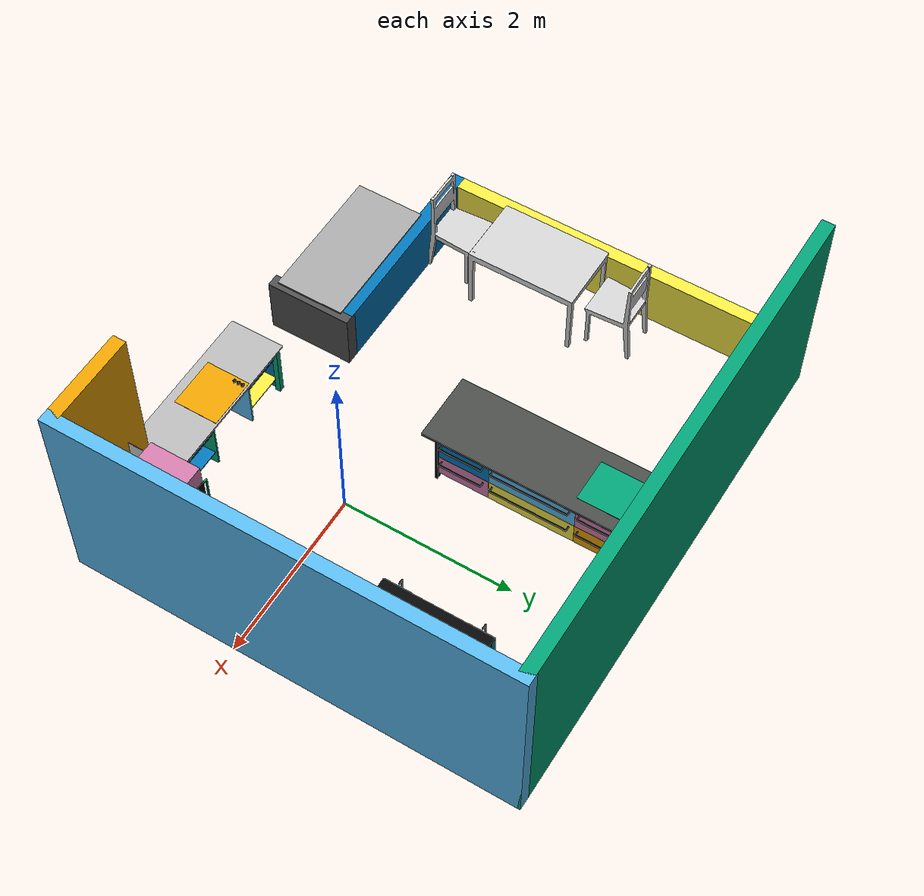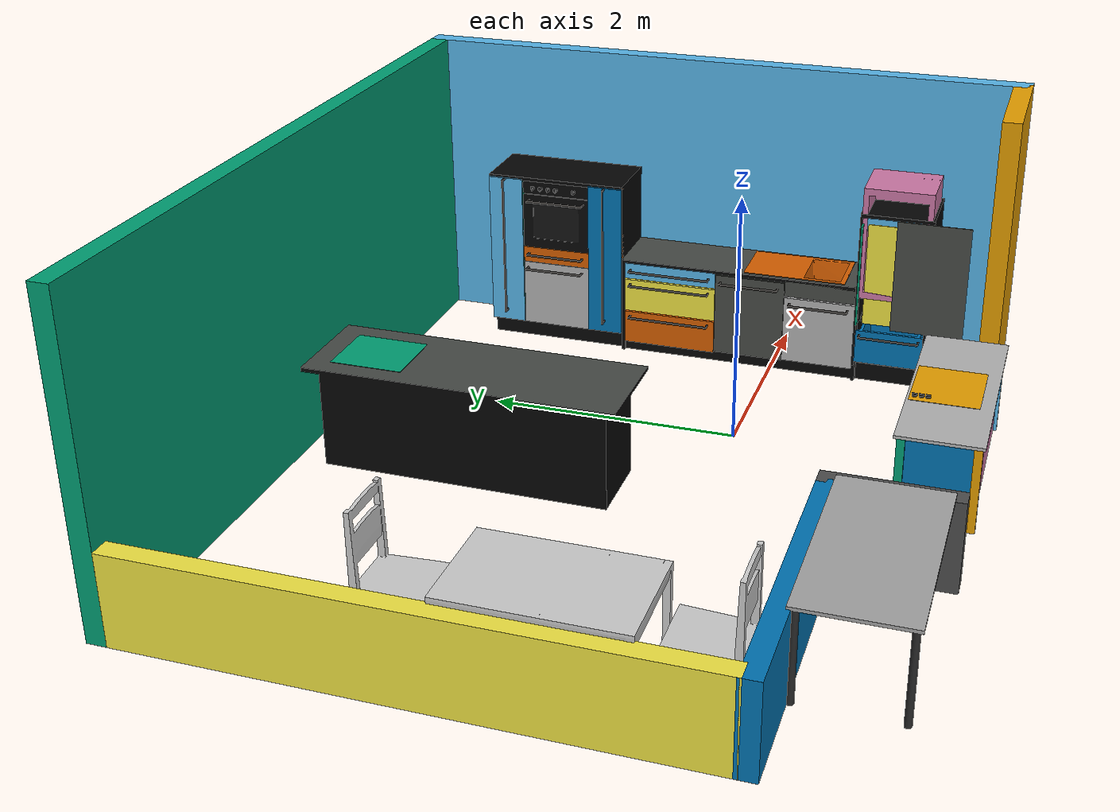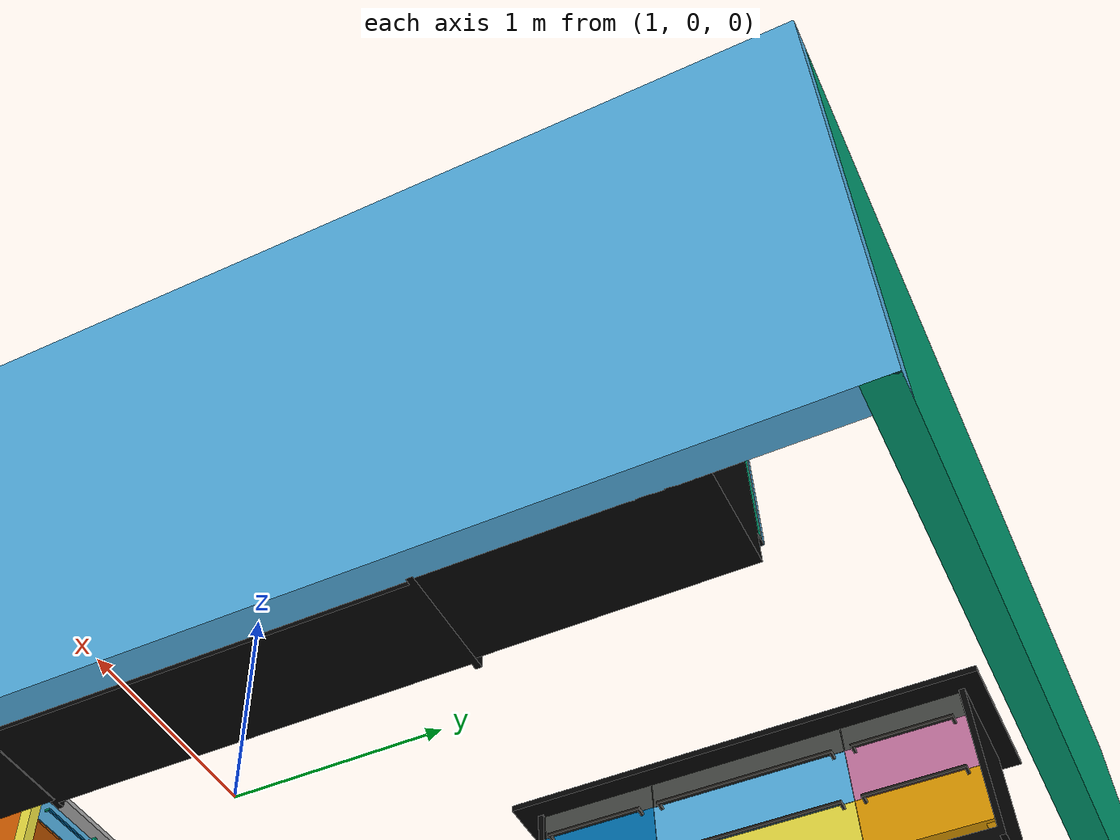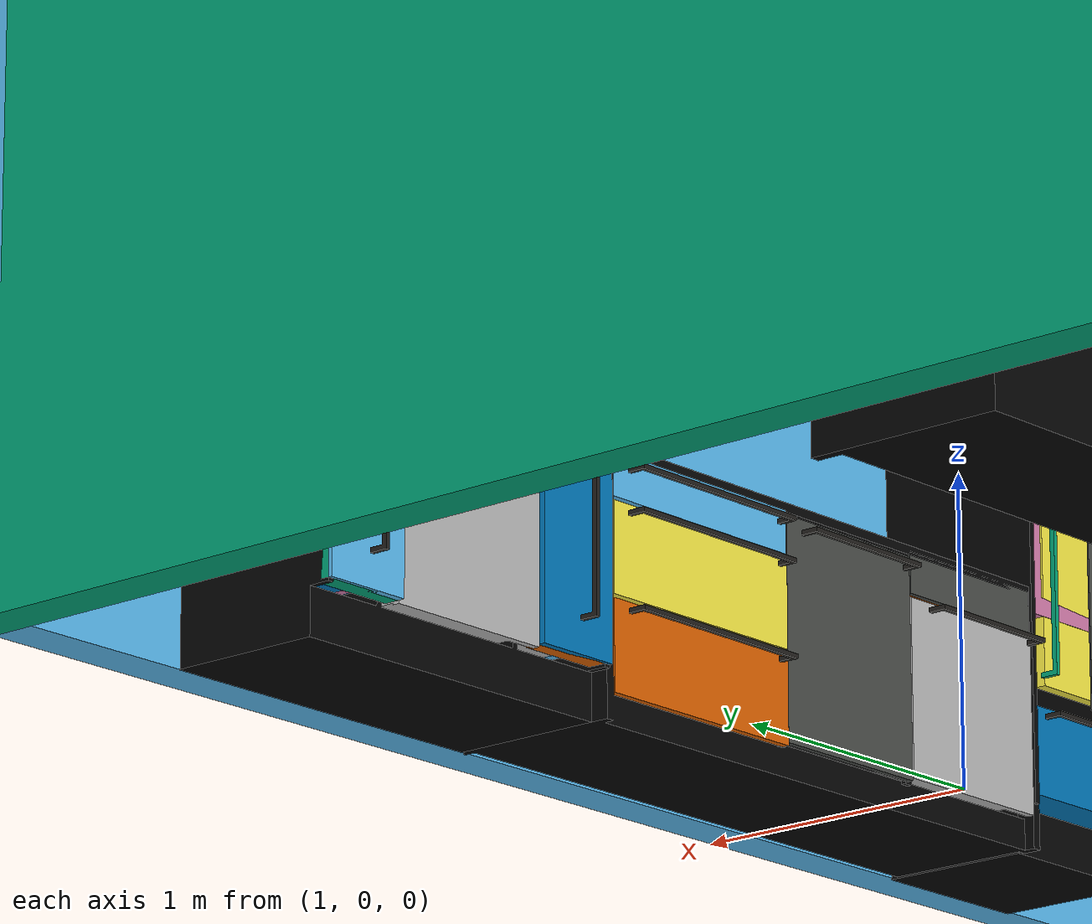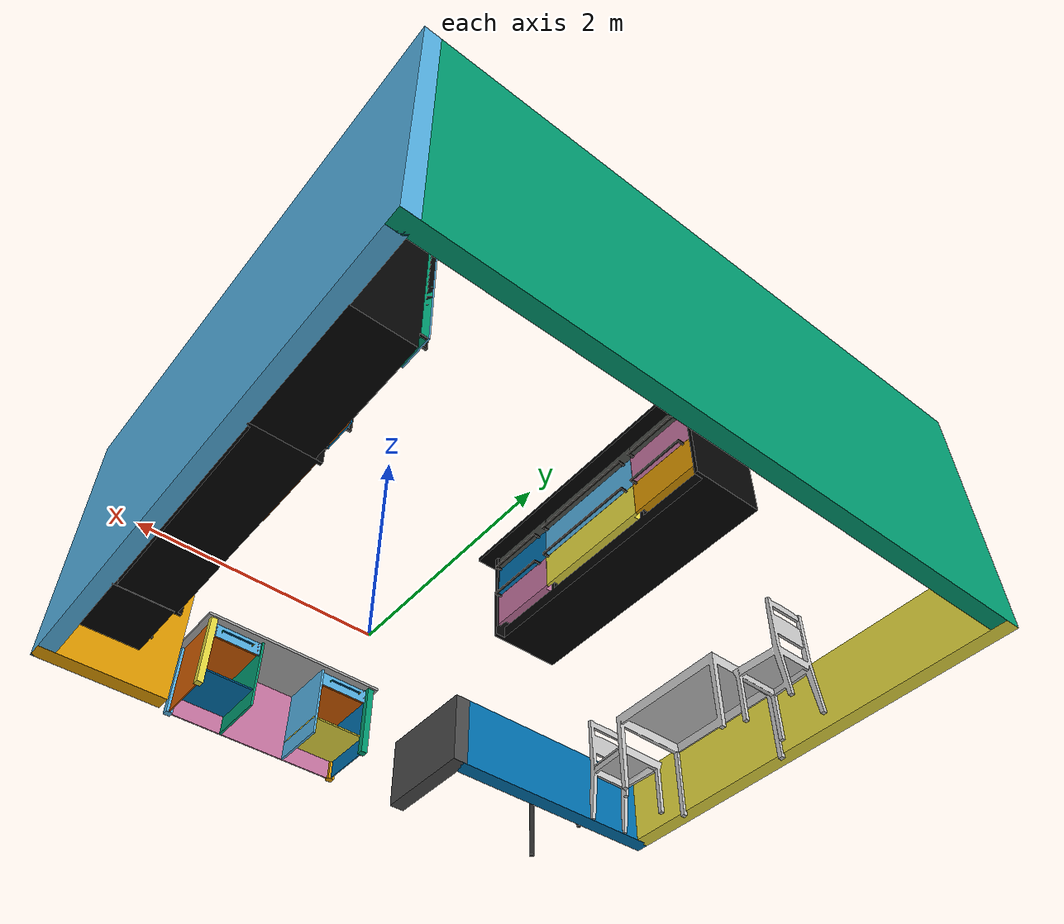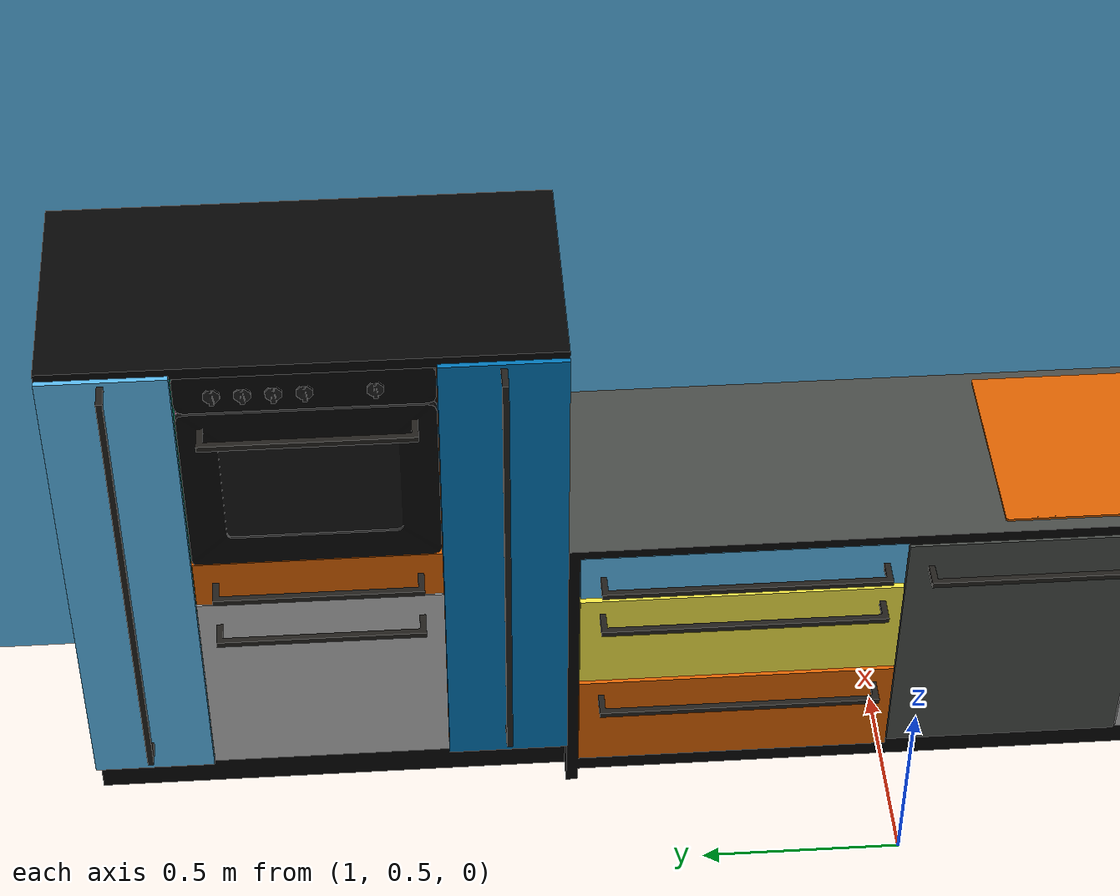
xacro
<?xml version="1.0"?>

<robot name="iai_kitchen" xmlns:xacro="http://ros.org/wiki/xacro">

  <!--- FIXME THIS should NOT be here -->
  <xacro:include filename="$(find iai_kitchen)/urdf_obj/IAI_oven_area.urdf.xacro"/>
  <xacro:include filename="$(find iai_kitchen)/urdf_obj/IAI_kitchen_island.urdf.xacro"/>
  <xacro:include filename="$(find iai_kitchen)/urdf_obj/IAI_sink_area.urdf.xacro"/>
  <xacro:include filename="$(find iai_kitchen)/urdf_obj/IAI_fridge_area.urdf.xacro"/>
  <xacro:include filename="$(find iai_kitchen)/urdf_obj/IAI_tables.urdf.xacro"/>
  <xacro:include filename="$(find iai_kitchen)/urdf_obj/IAI_kitchen_walls.urdf.xacro"/>
  <xacro:include filename="$(find iai_kitchen)/urdf_obj/IAI_popcorn_table.urdf.xacro"/>

  <xacro:property name="pi" value="3.1415926535897931" />
  <xacro:property name="simulated" value="true" />
  <xacro:property name="include_wall_7" value="false"/>

  <xacro:macro name="sphere_inertia" params="radius mass">
    <inertial>
      <origin xyz="0.0 0.0 0.0" rpy="0 0 0"/>
      <mass value="1"/>
      <inertia
          ixx="1" ixy="0.0" ixz="0.0"
          iyy="1" iyz="0.0"
          izz="1"/>
    </inertial>
  </xacro:macro>

  <link name="room_link">
    <sphere_inertia radius="0" mass="0"/>
  </link>
  <xacro:if value="${simulated}">
    <link name="world"/>
    <joint name="world_room_joint" type="fixed">
      <origin xyz="0.0 0.03 0 " rpy="0 0 0" />
      <parent link="world"/>
      <child link="room_link"/>
    </joint>
  </xacro:if>

  <xacro:iai_sink_area name="sink_area" parent="room_link">
    <origin xyz="1.855 1.3 0" rpy="0 0 ${pi}" />
  </xacro:iai_sink_area>

  <xacro:iai_oven_area name="oven_area" parent="room_link">
    <origin xyz="1.845 2.5 0" rpy="0 0 ${pi}" />
  </xacro:iai_oven_area>

  <xacro:iai_kitchen_island name="kitchen_island" parent="room_link">
    <origin xyz="-1.363 0.59 0" rpy="0 0 0" />
  </xacro:iai_kitchen_island>

  <xacro:iai_fridge_area name="fridge_area" parent="room_link">
    <origin xyz="1.845 -0.73 0" rpy="0 0 ${pi}" />
  </xacro:iai_fridge_area>

  <xacro:iai_table_1 name="table_area" parent="room_link">
    <origin xyz="-2.4 -1.5 0" rpy="0 0 ${pi}" />
  </xacro:iai_table_1>

  <xacro:iai_dining_area name="dining_area" parent="room_link">
    <origin xyz="-3.38 0.28 0" rpy="0 0 ${pi / 2}" />
  </xacro:iai_dining_area>

  <xacro:iai_kitchen_wall_robohow parent="room_link" include_wall_7="${include_wall_7}">
    <origin xyz="-0.96 0.65 0" rpy="0.0 0.0 0.0" />
  </xacro:iai_kitchen_wall_robohow>

  <xacro:iai_popcorn_table name="iai_popcorn_table" parent="room_link">
    <origin xyz="-0.05 -1.7 0"/>
  </xacro:iai_popcorn_table>

  <gazebo>
    <static>false</static>
  </gazebo>

</robot>

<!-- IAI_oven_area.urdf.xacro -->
<robot name="iai_oven_area" xmlns:xacro="http://ros.org/wiki/xacro">

  <xacro:property name="pi" value="3.1415926535897931" />

  <!--- FIXME THIS should NOT be here -->
  <xacro:include filename="$(find iai_kitchen)/urdf_obj/IAI_drawers.urdf.xacro"/>
  <xacro:include filename="$(find iai_kitchen)/urdf_obj/IAI_oven.urdf.xacro"/>

  <xacro:macro name="iai_oven_area" params="parent name *origin">
  <link name="${name}_area_footprint">
    <xacro:sphere_inertia radius="0" mass="0"/>
  </link>

  <link name="${name}_area">
    <xacro:sphere_inertia radius="0" mass="0"/>
    <visual>
        <origin xyz="0 0 0" rpy="0 0 0" />
        <geometry>
          <mesh filename="package://iai_kitchen/meshes/racks/OvenArea.dae"/>
        </geometry>
      </visual>
    <collision>
        <origin xyz="0 0 0" rpy="0 0 0" />
        <geometry>
          <mesh filename="package://iai_kitchen/meshes/racks/OvenArea.obj"/>
        </geometry>
      </collision>
  </link>

  <joint name="${name}_footprint_joint" type="fixed">
      <xacro:insert_block name="origin" />
    <child link="${name}_area_footprint"/>
    <parent link="${parent}"/>
  </joint>

  <joint name="${name}_main_joint" type="fixed">
    <origin xyz="0.29 0.6 0.755" rpy="0 0 0" />
    <parent link="${name}_area_footprint"/>
    <child link="${name}_area"/>
  </joint>

  <xacro:iai_oven name="${name}_oven" parent="${name}_area">
    <origin rpy="0 0 0" xyz="0.0 0.0 0.415"/>
  </xacro:iai_oven>

  <xacro:iai_drawer_60_14 name="${name}_area_middle_upper_drawer" parent="${name}_area">
    <origin rpy="0 0 0" xyz="0.0 -0. 0.045 "/>
  </xacro:iai_drawer_60_14>

  <xacro:iai_drawer_60_58 name="${name}_area_middle_lower_drawer" parent="${name}_area">
    <origin rpy="0 0 0" xyz="0.0 -0. -0.315 "/>
  </xacro:iai_drawer_60_58>

  <xacro:iai_vdrawer name="${name}_area_left_drawer" parent="${name}_area">
    <origin rpy="0 0 0" xyz="0.29 -0.45 0.07 "/>
  </xacro:iai_vdrawer>

  <xacro:iai_vdrawer name="${name}_area_right_drawer" parent="${name}_area">
    <origin rpy="0 0 0" xyz="0.29 0.45 0.07"/>
  </xacro:iai_vdrawer>

  </xacro:macro>

</robot>

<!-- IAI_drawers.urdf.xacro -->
<robot name="iai_drawers" xmlns:xacro="http://ros.org/wiki/xacro">

  <xacro:property name="pi" value="3.1415926535897931" />

  <xacro:macro name="iai_drawer_60_14" params="name parent *origin">
    <xacro:iai_drawer_14 name="${name}" parent="${parent}" width="60">
      <xacro:insert_block name="origin" />
    </xacro:iai_drawer_14>
  </xacro:macro>

  <xacro:macro name="iai_drawer_80_14" params="name parent *origin">
    <xacro:iai_drawer_14 name="${name}" parent="${parent}" width="80">
      <xacro:insert_block name="origin" />
    </xacro:iai_drawer_14>
  </xacro:macro>

  <xacro:macro name="iai_drawer_60_29" params="name parent *origin">
    <xacro:iai_drawer_29 name="${name}" parent="${parent}" width="60">
      <xacro:insert_block name="origin" />
    </xacro:iai_drawer_29>
  </xacro:macro>

  <xacro:macro name="iai_drawer_80_29" params="name parent *origin">
    <xacro:iai_drawer_29 name="${name}" parent="${parent}" width="80">
      <xacro:insert_block name="origin" />
    </xacro:iai_drawer_29>
  </xacro:macro>

  <xacro:macro name="iai_drawer_100_29" params="name parent *origin">
    <xacro:iai_drawer_29 name="${name}" parent="${parent}" width="100">
      <xacro:insert_block name="origin" />
    </xacro:iai_drawer_29>
  </xacro:macro>

  <xacro:macro name="iai_drawer_60_58" params="name parent *origin">
    <xacro:iai_drawer_58 name="${name}" parent="${parent}" width="60">
      <xacro:insert_block name="origin" />
    </xacro:iai_drawer_58>
  </xacro:macro>

  <xacro:macro name="iai_drawer_58" params="name parent width *origin">

    <xacro:iai_generic_drawer name="${name}" parent="${parent}" width="${width}" height="58">
      <xacro:insert_block name="origin" />
      <origin xyz="0.37 0 0.25" rpy="0 0 0" />
    </xacro:iai_generic_drawer>
  </xacro:macro>

  <xacro:property name="board_x" value="0.49"/>
  <xacro:property name="board_y" value="0.25"/>
  <xacro:property name="board_z" value="0.036"/>
  <xacro:property name="barrier_z" value="0.1"/>
  <xacro:macro name="iai_vdrawer_board" params="name parent joint_origin_z">
    <link name="${parent}_board_${name}_link">
      <sphere_inertia radius="0" mass="0"/>
      <visual>
        <origin rpy="0 0 0" xyz="0 0 0"/>
        <geometry>
          <box size="${board_x} ${board_y} ${board_z}"/>
        </geometry>
      </visual>
      <collision>
        <origin rpy="0 0 0" xyz="0 0 0"/>
        <geometry>
          <box size="${board_x} ${board_y} ${board_z}"/>
        </geometry>
      </collision>
    </link>

    <joint name="${parent}_board_${name}_joint" type="fixed">
      <origin xyz="${-board_y} 0 ${joint_origin_z}"/>
      <parent link="${parent}_main"/>
      <child link="${parent}_board_${name}_link"/>
    </joint>

    <link name="${parent}_barrier_${name}_right_link">
      <sphere_inertia radius="0" mass="0"/>
      <visual>
        <origin rpy="0 0 0" xyz="0 0 0"/>
        <geometry>
          <box size="${board_x} ${board_z} ${barrier_z}"/>
        </geometry>
      </visual>
      <collision>
        <origin rpy="0 0 0" xyz="0 0 0"/>
        <geometry>
          <box size="${board_x} ${board_z} ${barrier_z}"/>
        </geometry>
      </collision>
    </link>

    <joint name="${parent}_barrier_${name}_right_joint" type="fixed">
      <origin xyz="${-board_y} ${-board_y / 2 + board_z / 2} ${joint_origin_z + barrier_z/2 - board_z/2}"/>
      <parent link="${parent}_main"/>
      <child link="${parent}_barrier_${name}_right_link"/>
    </joint>

    <link name="${parent}_barrier_${name}_left_link">
      <sphere_inertia radius="0" mass="0"/>
      <visual>
        <origin rpy="0 0 0" xyz="0 0 0"/>
        <geometry>
          <box size="${board_x} ${board_z} ${barrier_z}"/>
        </geometry>
      </visual>
      <collision>
        <origin rpy="0 0 0" xyz="0 0 0"/>
        <geometry>
          <box size="${board_x} ${board_z} ${barrier_z}"/>
        </geometry>
      </collision>
    </link>

    <joint name="${parent}_barrier_${name}_left_joint" type="fixed">
      <origin xyz="${-board_y} ${board_y / 2 - board_z / 2} ${joint_origin_z + barrier_z/2 - board_z/2}"/>
      <parent link="${parent}_main"/>
      <child link="${parent}_barrier_${name}_left_link"/>
    </joint>

    <link name="${parent}_barrier_${name}_back_link">
      <sphere_inertia radius="0" mass="0"/>
      <visual>
        <origin rpy="0 0 0" xyz="0 0 0"/>
        <geometry>
          <box size="${board_z} ${board_y} ${barrier_z}"/>
        </geometry>
      </visual>
      <collision>
        <origin rpy="0 0 0" xyz="0 0 0"/>
        <geometry>
          <box size="${board_z} ${board_y} ${barrier_z}"/>
        </geometry>
      </collision>
    </link>

    <joint name="${parent}_barrier_${name}_back_joint" type="fixed">
      <origin xyz="${-board_x / 2 + board_z / 2 - board_y} 0 ${joint_origin_z + barrier_z/2 - board_z/2}"/>
      <parent link="${parent}_main"/>
      <child link="${parent}_barrier_${name}_back_link"/>
    </joint>
  </xacro:macro>

  <xacro:macro name="iai_vdrawer" params="name parent *origin">
    <joint name="${name}_main_joint" type="prismatic">
      <xacro:insert_block name="origin"/>
      <parent link="${parent}"/>
      <child link="${name}_main"/>
      <axis xyz="1. 0. 0.0"/>
      <limit effort="300" lower="0" upper="0.48" velocity="10"/>
    </joint>

    <link name="${name}_main">
      <sphere_inertia radius="0" mass="0"/>
      <visual>
        <origin rpy="0 0 0" xyz="0 0 0"/>
        <geometry>
          <box size="0.025 0.3 1.33"/>
        </geometry>
      </visual>
      <collision>
        <origin rpy="0 0 0" xyz="0 0 0"/>
        <geometry>
          <box size="0.025 0.3 1.33"/>
        </geometry>
      </collision>
    </link>

    <joint name="${name}_main_padding_joint" type="fixed">
      <parent link="${name}_main"/>
      <child link="${name}_main_padding"/>
      <origin rpy="0 0 0" xyz="-0.03 0.0 0.0"/>
    </joint>
    <link name="${name}_main_padding">
      <sphere_inertia radius="0" mass="0"/>
      <visual>
        <origin rpy="0 0 0" xyz="0 0 0"/>
        <geometry>
          <box size="0.06 0.3 1.33"/>
        </geometry>
      </visual>
      <collision>
        <origin rpy="0 0 0" xyz="0 0 0"/>
        <geometry>
          <box size="0.06 0.3 1.33"/>
        </geometry>
      </collision>
    </link>

    <joint name="${name}_handle_joint" type="fixed">
      <origin rpy="${-0.5*pi} 0 0" xyz="0.08 0.0 0.05"/>
      <parent link="${name}_main" />
      <child link="${name}_handle" />
    </joint>

    <link name="${name}_handle">
      <sphere_inertia radius="0" mass="0"/>
      <visual>
        <origin xyz="0 0 0" rpy="${0.5*pi} 0 0" />
        <geometry>
          <mesh filename="package://iai_kitchen/meshes/handles/VHandle130.obj"/>
        </geometry>
      </visual>
      <collision>
        <origin xyz="0 0 0" rpy="${0.5*pi} 0 0" />
        <geometry>
          <mesh filename="package://iai_kitchen/meshes/handles/VHandle130.obj"/>
        </geometry>
      </collision>
    </link>

    <xacro:iai_vdrawer_board name="0" parent="${name}" joint_origin_z="-0.6"/>
    <xacro:iai_vdrawer_board name="1" parent="${name}" joint_origin_z="-0.28"/>
    <xacro:iai_vdrawer_board name="2" parent="${name}" joint_origin_z="0.05"/>
    <xacro:iai_vdrawer_board name="3" parent="${name}" joint_origin_z="0.38"/>
  </xacro:macro>

  <xacro:macro name="iai_drawer_29" params="name parent width *origin">

    <xacro:iai_generic_drawer name="${name}" parent="${parent}" width="${width}" height="29">
      <xacro:insert_block name="origin" />
      <origin xyz="0.3525 0 0.11" rpy="0 0 0" />
    </xacro:iai_generic_drawer>
  </xacro:macro>

  <xacro:macro name="iai_drawer_14" params="name parent width *origin">

    <xacro:iai_generic_drawer name="${name}" parent="${parent}" width="${width}" height="14">
      <xacro:insert_block name="origin" />
      <origin xyz="0.3525 0 0.0175" rpy="0 0 0" />
    </xacro:iai_generic_drawer>
  </xacro:macro>

  <xacro:macro name="iai_generic_drawer" params="name parent width height *origin *handle_origin">
    <link name="${name}_main">
      <sphere_inertia radius="0" mass="0"/>
      <visual>
        <origin xyz="0 0 0" rpy="0 0 0" />
        <geometry>
          <mesh filename="package://iai_kitchen/meshes/drawers/Drawer_${width}_${height}.obj"/>
        </geometry>
      </visual>
      <collision>
        <origin xyz="0 0 0" rpy="0 0 0" />
        <geometry>
          <mesh filename="package://iai_kitchen/meshes/drawers/Drawer_${width}_${height}.obj"/>
        </geometry>
      </collision>
    </link>

    <link name="${name}_handle">
      <sphere_inertia radius="0" mass="0"/>
      <visual>
        <origin xyz="0 0 0" rpy="0 0 0" />
        <geometry>
          <mesh filename="package://iai_kitchen/meshes/handles/Handle${width}.obj"/>
        </geometry>
      </visual>
      <collision>
        <origin xyz="0 0 0" rpy="0 0 0" />
        <geometry>
          <mesh filename="package://iai_kitchen/meshes/handles/Handle${width}.obj"/>
        </geometry>
      </collision>
    </link>

    <joint name="${name}_main_joint" type="prismatic">
      <xacro:insert_block name="origin" />
      <parent link="${parent}"/>
      <child link="${name}_main"/>
      <axis xyz="1. 0. 0.0"/>
      <limit effort="300" lower="0" upper="0.48" velocity="10"/>
    </joint>

    <joint name="${name}_handle_joint" type="fixed">
      <xacro:insert_block name="handle_origin"/>
      <parent link="${name}_main"/>
      <child link="${name}_handle"/>
      <axis xyz="0 0 1"/>
      <limit lower="0" upper="${0.5*pi}" effort="300" velocity="10"/>
    </joint>
  </xacro:macro>

  <xacro:macro name="iai_generic_panel" params="name parent width *origin">
    <link name="${name}">
      <sphere_inertia radius="0" mass="0"/>
      <visual>
        <origin xyz="0 0 0" rpy="0 0 0" />
        <geometry>
          <mesh filename="package://iai_kitchen/meshes/drawers/Panel_${width}.obj"/>
        </geometry>
      </visual>
      <collision>
        <origin xyz="0 0 0" rpy="0 0 0" />
        <geometry>
          <mesh filename="package://iai_kitchen/meshes/drawers/Panel_${width}.obj"/>
        </geometry>
      </collision>
    </link>

    <joint name="${name}_joint" type="fixed">
      <xacro:insert_block name="origin"/>
      <parent link="${parent}"/>
      <child link="${name}"/>
    </joint>
  </xacro:macro>

  <!--- FIXME THIS should NOT be here -->
</robot>

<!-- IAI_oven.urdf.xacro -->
<robot name="iai_oven" xmlns:xacro="http://ros.org/wiki/xacro">

  <xacro:property name="pi" value="3.1415926535897931" />

  <xacro:macro name="iai_oven" params="name parent *origin">
    <!-- LINKS -->

    <link name="${name}_main">

      <xacro:sphere_inertia radius="0" mass="0"/>
      <visual>
        <origin xyz="0 0 0" rpy="0 0 0" />
        <geometry>
          <mesh filename="package://iai_kitchen/meshes/oven/OvenMain.dae"/>
        </geometry>
      </visual>
      <collision>
        <origin xyz="0 0 0" rpy="0 0 0" />
        <geometry>
          <mesh filename="package://iai_kitchen/meshes/oven/OvenMain.obj"/>
        </geometry>
      </collision>
    </link>

    <link name="${name}_door">

      <xacro:sphere_inertia radius="0" mass="0"/>
      <visual>
        <origin xyz="0 0 0" rpy="${0.5*pi} 0 0" />
        <geometry>
          <mesh filename="package://iai_kitchen/meshes/oven/OvenDoor.dae"/>
        </geometry>
      </visual>
      <collision>
        <origin xyz="0 0 0" rpy="${0.5*pi} 0 0" />
        <geometry>
          <mesh filename="package://iai_kitchen/meshes/oven/OvenDoor.obj"/>
        </geometry>
      </collision>
    </link>

    <link name="${name}_door_handle">

      <xacro:sphere_inertia radius="0" mass="0"/>
      <visual>
        <origin xyz="0 0 0" rpy="0 0 0" />
        <geometry>
          <mesh filename="package://iai_kitchen/meshes/handles/Handle60.dae"/>
        </geometry>
      </visual>
      <collision>
        <origin xyz="0 0 0" rpy="0 0 0" />
        <geometry>
          <mesh filename="package://iai_kitchen/meshes/handles/Handle60.obj"/>
        </geometry>
      </collision>
    </link>

    <link name="${name}_panel">

      <xacro:sphere_inertia radius="0" mass="0"/>
      <visual>
        <origin xyz="0 0 0" rpy="0 0 0" />
        <geometry>
          <mesh filename="package://iai_kitchen/meshes/oven/OvenPanel.dae"/>
        </geometry>
      </visual>
      <collision>
        <origin xyz="0 0 0" rpy="0 0 0" />
        <geometry>
          <mesh filename="package://iai_kitchen/meshes/oven/OvenPanel.obj"/>
        </geometry>
      </collision>
    </link>

    <!-- JOINTS -->

    <joint name="${name}_main_joint" type="fixed">
      <xacro:insert_block name="origin" />
      <parent link="${parent}"/>
      <child link="${name}_main"/>
    </joint>
    <xacro:if value="${simulated}">
      <joint name="${name}_door_joint" type="revolute">
        <origin xyz="0.2737 0. -0.2614" rpy="${-0.5*pi} 0 0" />
        <parent link="${name}_main"/>
        <child link="${name}_door"/>
        <axis xyz="0 0 1"/>
        <!-- FIXME make the closed position stable -->
        <limit lower="0" upper="${0.5*pi}" effort="0.03" velocity="10"/>

        <dynamics damping="100.1"/>
      </joint>
      <gazebo reference="${name}_door_joint">
        <kp>1000000000</kp>
        <kd>1000000000</kd>
      </gazebo>
    </xacro:if>
    <xacro:unless value="${simulated}">
      <joint name="${name}_door_joint" type="revolute">
        <origin xyz="0.2737 0. -0.2614" rpy="${-0.5*pi} 0 0" />
        <parent link="${name}_main"/>
        <child link="${name}_door"/>
        <axis xyz="0 0 1"/>

        <limit lower="0" upper="${0.5*pi}" effort="300" velocity="10"/>

      </joint>

    </xacro:unless>
    <joint name="${name}_door_handle_joint" type="fixed">
      <origin xyz="0.05876 -0.39803 0." rpy="${-0.5*pi} 0 0" />
      <parent link="${name}_door"/>
      <child link="${name}_door_handle"/>
      <axis xyz="0 0 1"/>
      <limit lower="0" upper="${0.5*pi}" effort="300" velocity="10"/>
    </joint>

    <joint name="${name}_panel_joint" type="fixed">
      <origin xyz="0.27 0 0.2449" rpy="0 0 0" />
      <parent link="${name}_main"/>
      <child link="${name}_panel"/>
    </joint>

    <!--KNOBS -->

    <xacro:iai_oven_knob name="${name}_knob_stove_2" parent="${name}_panel" xyz="0 -0.14 0"/>
    <xacro:iai_oven_knob name="${name}_knob_stove_1" parent="${name}_panel" xyz="0 -0.21 0"/>
    <xacro:iai_oven_knob name="${name}_knob_stove_3" parent="${name}_panel" xyz="0 -0.07 0"/>
    <xacro:iai_oven_knob name="${name}_knob_stove_4" parent="${name}_panel" xyz="0 -0.0 0"/>
    <xacro:iai_oven_knob name="${name}_knob_oven" parent="${name}_panel" xyz="0 0.16 0"/>

  </xacro:macro>

  <xacro:macro name="iai_oven_knob" params="name parent xyz">
    <link name="${name}">

      <xacro:sphere_inertia radius="0" mass="0"/>
      <visual>
        <origin xyz="0 0 0" rpy="0 ${0.5 * pi} 0" />
        <geometry>
          <mesh filename="package://iai_kitchen/meshes/oven/Knob.dae"/>
        </geometry>
      </visual>
      <collision>
        <origin xyz="0 0 0" rpy="0 ${0.5 * pi} 0" />
        <geometry>
          <mesh filename="package://iai_kitchen/meshes/oven/Knob.obj"/>
        </geometry>
      </collision>
    </link>

    <joint name="${name}_joint" type="revolute">
      <origin xyz="${xyz}" rpy="0 ${-0.5 * pi} 0" />
      <parent link="${parent}"/>
      <child link="${name}"/>
      <axis xyz="0 0 1"/>
      <limit lower="0" upper="${pi}" effort="300" velocity="10"/>
    </joint>

  </xacro:macro>

  <!--- FIXME THIS should NOT be here -->
</robot>

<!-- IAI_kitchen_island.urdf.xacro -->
<robot name="iai_kitchen_island" xmlns:xacro="http://ros.org/wiki/xacro">

  <xacro:property name="pi" value="3.1415926535897931" />

  <!--- FIXME THIS should NOT be here -->
  <xacro:include filename="$(find iai_kitchen)/urdf_obj/IAI_drawers.urdf.xacro"/>

  <xacro:macro name="iai_kitchen_island" params="parent name *origin">

    <link name="${name}_footprint">
      <xacro:sphere_inertia radius="0" mass="0"/>
    </link>
    <link name="${name}">
      <xacro:sphere_inertia radius="0" mass="0"/>
      <visual>
        <origin xyz="0 0 0" rpy="0 0 0" />
        <geometry>
          <mesh filename="package://iai_kitchen/meshes/racks/IslandArea.dae"/>
        </geometry>
      </visual>
      <collision>
        <origin xyz="0 0 0" rpy="0 0 0" />
        <geometry>
          <mesh filename="package://iai_kitchen/meshes/racks/IslandArea.obj"/>
        </geometry>
      </collision>
    </link>

    <joint name="${name}_footprint_joint" type="fixed">
        <xacro:insert_block name="origin" />
      <child link="${name}_footprint"/>
      <parent link="${parent}"/>
    </joint>

    <joint name="${name}_joint" type="fixed">
      <origin xyz="0.2975 1.1292 0.421" rpy="0 0 0" />
      <parent link="${name}_footprint"/>
      <child link="${name}"/>
    </joint>

    <link name="${name}_surface">
      <xacro:sphere_inertia radius="0" mass="0"/>
      <collision>
          <origin xyz="0 0 0" rpy="0 0 0" />
          <geometry>
            <box size="0.8 2.45 0.02"/>
          </geometry>
        </collision>
    </link>

    <joint name="${name}_surface_joint" type="fixed">
      <origin xyz="0.0 0. 0.42" rpy="0 0 0" />
      <parent link="${name}"/>
      <child link="${name}_surface"/>
    </joint>

    <link name="${name}_stove">
      <xacro:sphere_inertia radius="0" mass="0"/>
      <visual>
          <origin xyz="0 0 0" rpy="0 0 0" />
          <geometry>
            <mesh filename="package://iai_kitchen/meshes/misc/Stove.dae"/>
          </geometry>
        </visual>
        <collision>
          <origin xyz="0 0 0" rpy="0 0 0" />
          <geometry>
            <mesh filename="package://iai_kitchen/meshes/misc/Stove.obj"/>
          </geometry>
        </collision>
    </link>

    <joint name="${name}_stove_joint" type="fixed">
      <origin xyz="0.0 0.7658 0.4315" rpy="0 0 0" />
      <parent link="${name}"/>
      <child link="${name}_stove"/>
    </joint>

    <xacro:iai_generic_panel name="${name}_left_panel" parent="${name}" width="60">
      <origin rpy="0 0 0" xyz="0.2725 -0.8 0.329 "/>
    </xacro:iai_generic_panel>
    <xacro:iai_drawer_60_29 name="${name}_left_upper_drawer" parent="${name}">
      <origin rpy="0 0 0" xyz="0.0025 -0.8 0.114 "/>
    </xacro:iai_drawer_60_29>
    <xacro:iai_drawer_60_29 name="${name}_left_lower_drawer" parent="${name}">
      <origin rpy="0 0 0" xyz="0.0025 -0.8 -0.176 "/>
    </xacro:iai_drawer_60_29>

    <xacro:iai_generic_panel name="${name}_middle_panel" parent="${name}" width="100">
      <origin rpy="0 0 0" xyz="0.2725 0 0.329 "/>
    </xacro:iai_generic_panel>
    <xacro:iai_drawer_100_29 name="${name}_middle_upper_drawer" parent="${name}">
      <origin rpy="0 0 0" xyz="0.0025 0 0.114 "/>
    </xacro:iai_drawer_100_29>
    <xacro:iai_drawer_100_29 name="${name}_middle_lower_drawer" parent="${name}">
      <origin rpy="0 0 0" xyz="0.0025 0 -0.176 "/>
    </xacro:iai_drawer_100_29>

    <xacro:iai_generic_panel name="${name}_right_panel" parent="${name}" width="60">
      <origin rpy="0 0 0" xyz="0.2725 0.8 0.329 "/>
    </xacro:iai_generic_panel>
    <xacro:iai_drawer_60_29 name="${name}_right_upper_drawer" parent="${name}">
      <origin rpy="0 0 0" xyz="0.0025 0.8 0.114 "/>
    </xacro:iai_drawer_60_29>
    <xacro:iai_drawer_60_29 name="${name}_right_lower_drawer" parent="${name}">
      <origin rpy="0 0 0" xyz="0.0025 0.8 -0.176 "/>
    </xacro:iai_drawer_60_29>
  </xacro:macro>
</robot>

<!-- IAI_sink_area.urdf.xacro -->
<robot name="iai_sink_area" xmlns:xacro="http://ros.org/wiki/xacro">

  <xacro:property name="pi" value="3.1415926535897931" />

  <!--- FIXME THIS should NOT be here -->
  <xacro:include filename="$(find iai_kitchen)/urdf_obj/IAI_drawers.urdf.xacro"/>
  <xacro:include filename="$(find iai_kitchen)/urdf_obj/IAI_dish_washer.urdf.xacro"/>

  <xacro:macro name="iai_sink_area" params="parent name *origin">
  <link name="${name}_footprint">
    <xacro:sphere_inertia radius="0" mass="0"/>
  </link>

  <link name="${name}">
    <xacro:sphere_inertia radius="0" mass="0"/>
    <visual>
        <origin xyz="0 0 0" rpy="0 0 0" />
        <geometry>
          <mesh filename="package://iai_kitchen/meshes/racks/SinkArea.dae"/>
        </geometry>
      </visual>
    <collision>
        <origin xyz="0 0 0" rpy="0 0 0" />
        <geometry>
          <mesh filename="package://iai_kitchen/meshes/racks/SinkArea.obj"/>
        </geometry>
      </collision>
  </link>

  <joint name="${name}_footprint_joint" type="fixed">
      <xacro:insert_block name="origin" />
    <child link="${name}_footprint"/>
    <parent link="${parent}"/>
  </joint>

  <joint name="${name}_main_joint" type="fixed">
    <origin xyz="0.29 1.03 0.41" rpy="0 0 0" />
    <parent link="${name}_footprint"/>
    <child link="${name}"/>
  </joint>

  <link name="${name}_surface">
    <xacro:sphere_inertia radius="0" mass="0"/>
    <collision>
      <origin xyz="0 -0.225 0" rpy="0 0 0" />
      <geometry>
        <box size="0.575 1.6 0.02"/>
      </geometry>
    </collision>
  </link>

 <joint name="${name}_surface_joint" type="fixed">
    <origin xyz="0.0 0. 0.43" rpy="0 0 0" />
    <parent link="${name}"/>
    <child link="${name}_surface"/>
 </joint>

  <link name="${name}_sink">
    <xacro:sphere_inertia radius="0" mass="0"/>
    <visual>
      <origin xyz="0 0 0" rpy="0 0 0" />
      <geometry>
        <mesh filename="package://iai_kitchen/meshes/misc/Sink.dae"/>
      </geometry>
    </visual>
    <collision>
      <origin xyz="0 0 0" rpy="0 0 0" />
      <geometry>
        <mesh filename="package://iai_kitchen/meshes/misc/Sink.obj"/>
      </geometry>
    </collision>
  </link>

  <joint name="${name}_sink_joint" type="fixed">
    <origin xyz="0.005 0.47 0.4414" rpy="0 0 0" />
    <parent link="${name}"/>
    <child link="${name}_sink"/>
  </joint>

  <xacro:iai_generic_panel name="${name}_right_panel" parent="${name}" width="60">
    <origin rpy="0 0 0" xyz="0.28 0.7 0.355 "/>
  </xacro:iai_generic_panel>
  <xacro:iai_drawer_60_58 name="${name}_trash_drawer" parent="${name}">
    <origin rpy="0 0 0" xyz="0.01 0.7 -0.015 "/>
  </xacro:iai_drawer_60_58>
  <xacro:iai_drawer_80_14 name="${name}_left_upper_drawer" parent="${name}">
    <origin rpy="0 0 0" xyz="0.01 -0.6 0.345 "/>
  </xacro:iai_drawer_80_14>
  <xacro:iai_drawer_80_29 name="${name}_left_middle_drawer" parent="${name}">
    <origin rpy="0 0 0" xyz="0.01 -0.6 0.12 "/>
  </xacro:iai_drawer_80_29>
  <xacro:iai_drawer_80_29 name="${name}_left_bottom_drawer" parent="${name}">
    <origin rpy="0 0 0" xyz="0.01 -0.6 -0.18" />
  </xacro:iai_drawer_80_29>
  <xacro:iai_dish_washer name="${name}_dish_washer" parent="${name}">
    <origin rpy="0 0 0" xyz="0.01 0.1 0.06" />
  </xacro:iai_dish_washer>
  </xacro:macro>

</robot>

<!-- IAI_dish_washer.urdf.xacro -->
<robot name="iai_dish_washer" xmlns:xacro="http://ros.org/wiki/xacro">

  <xacro:property name="pi" value="3.1415926535897931" />

  <xacro:macro name="iai_dish_washer" params="name parent *origin">
     <link name="${name}_main">

      <xacro:sphere_inertia radius="0" mass="0"/>
      <visual>
        <origin xyz="0 0 0" rpy="0 0 0" />
        <geometry>
          <mesh filename="package://iai_kitchen/meshes/misc/DishWasher.dae"/>
        </geometry>
      </visual>
      <collision>
        <origin xyz="0 0 0" rpy="0 0 0" />
        <geometry>
          <mesh filename="package://iai_kitchen/meshes/misc/DishWasher.obj"/>
        </geometry>
      </collision>
    </link>

    <link name="${name}_door">

      <xacro:sphere_inertia radius="0" mass="0"/>
      <visual>
        <origin xyz="0 0.055 0" rpy="${0.5*pi} 0 0" />
        <geometry>
          <mesh filename="package://iai_kitchen/meshes/misc/DishWasherDoor.dae"/>
        </geometry>
      </visual>
      <collision>
        <origin xyz="0 0.055 0" rpy="${0.5*pi} 0 0" />
        <geometry>
          <mesh filename="package://iai_kitchen/meshes/misc/DishWasherDoor.obj"/>
        </geometry>
      </collision>
    </link>

    <link name="${name}_door_handle">
      <xacro:sphere_inertia radius="0" mass="0"/>
      <visual>
        <origin xyz="0 0 0" rpy="0 0 0" />
        <geometry>
          <mesh filename="package://iai_kitchen/meshes/handles/Handle60.dae"/>
        </geometry>
      </visual>
      <collision>
        <origin xyz="0 0 0" rpy="0 0 0" />
        <geometry>
          <mesh filename="package://iai_kitchen/meshes/handles/Handle60.obj"/>
        </geometry>
      </collision>
    </link>
    <joint name="${name}_main_joint" type="fixed">
      <xacro:insert_block name="origin" />
      <parent link="${parent}"/>
      <child link="${name}_main"/>
    </joint>

    <joint name="${name}_door_joint" type="revolute">
      <origin xyz="0.27 0. -0.285" rpy="${-0.5*pi} 0 0" />
      <parent link="${name}_main"/>
      <child link="${name}_door"/>
      <axis xyz="0 0 1"/>
      <limit lower="0" upper="${0.5*pi}" effort="300" velocity="10"/>
    </joint>
    <joint name="${name}_door_handle_joint" type="fixed">
      <origin xyz="0.085 -0.575 0.0" rpy="${-0.5*pi} 0 0" />
      <parent link="${name}_door"/>
      <child link="${name}_door_handle"/>
    </joint>

    <xacro:dishwasher_tray name="${name}_tray" parent="${name}_main">
      <origin xyz="-0.08 0 0.15"/>
    </xacro:dishwasher_tray>

  </xacro:macro>

  <xacro:macro name="dishwasher_tray" params="name parent *origin">

    <joint name="${name}_main" type="prismatic">
      <xacro:insert_block name="origin"/>
      <parent link="${parent}"/>
      <child link="${name}_bottom"/>
      <axis xyz="1 0 0"/>
      <limit lower="0" upper="0.48" effort="300" velocity="10"/>
    </joint>

    <link name="${name}_bottom">
      <visual>
        <geometry>
          <box size="0.32 0.5 0.05"/>
        </geometry>
      </visual>
      <collision>
        <geometry>
          <box size="0.32 0.5 0.05"/>
        </geometry>
      </collision>
    </link>

    <link name="${name}_left_side">
      <visual>
        <geometry>
          <box size="0.32 0.005 0.17"/>
        </geometry>
      </visual>
      <collision>
        <geometry>
          <box size="0.32 0.005 0.17"/>
        </geometry>
      </collision>
    </link>

    <link name="${name}_right_side">
      <visual>
        <geometry>
          <box size="0.32 0.005 0.17"/>
        </geometry>
      </visual>
      <collision>
        <geometry>
          <box size="0.32 0.005 0.17"/>
        </geometry>
      </collision>
    </link>

    <link name="${name}_back_side">
      <visual>
        <geometry>
          <box size="0.005 0.5 0.17"/>
        </geometry>
      </visual>
      <collision>
        <geometry>
          <box size="0.005 0.5 0.17"/>
        </geometry>
      </collision>
    </link>

    <link name="${name}_front_side">
      <visual>
        <geometry>
          <box size="0.005 0.5 0.17"/>
        </geometry>
      </visual>
      <collision>
        <geometry>
          <box size="0.005 0.5 0.17"/>
        </geometry>
      </collision>
    </link>

    <joint name="${name}_bottom_left" type="fixed">
      <origin xyz="-0.0 -0.25 0.075"/>
      <child link="${name}_left_side" />
      <parent link="${name}_bottom"/>
    </joint>

    <joint name="${name}_bottom_right" type="fixed">
      <origin xyz="-0.0 0.25 0.075"/>
      <child link="${name}_right_side" />
      <parent link="${name}_bottom"/>
    </joint>

    <joint name="${name}_bottom_back" type="fixed">
      <origin xyz="-0.16 0 0.075"/>
      <child link="${name}_back_side" />
      <parent link="${name}_bottom"/>
    </joint>

    <joint name="${name}_bottom_front" type="fixed">
      <origin xyz="0.16 0 0.075"/>
      <child link="${name}_front_side" />
      <parent link="${name}_bottom"/>
    </joint>

    <xacro:tray_handle name="${name}_handle" parent="${name}_front_side">
      <origin xyz="0.06 -0.1 -0.02"/>
    </xacro:tray_handle>

  </xacro:macro>

  <xacro:macro name="tray_handle" params="name parent *origin">

    <joint name="${name}_joint" type="fixed">
      <xacro:insert_block name="origin"/>
      <child link="${name}_front_side" />
      <parent link="${parent}"/>
    </joint>

    <link name="${name}_left_side">
      <visual>
        <geometry>
          <box size="0.03 0.01 0.01"/>
        </geometry>
      </visual>
      <collision>
        <geometry>
          <box size="0.03 0.01 0.01"/>
        </geometry>
      </collision>
    </link>

    <link name="${name}_right_side">
      <visual>
        <geometry>
          <box size="0.03 0.01 0.01"/>
        </geometry>
      </visual>
      <collision>
        <geometry>
          <box size="0.03 0.01 0.01"/>
        </geometry>
      </collision>
    </link>

    <link name="${name}_front_side">
      <visual>
        <geometry>
          <box size="0.01 0.2 0.01"/>
        </geometry>
      </visual>
      <collision>
        <geometry>
          <box size="0.01 0.2 0.01"/>
        </geometry>
      </collision>
    </link>

    <joint name="${name}_front_left_joint" type="fixed">
      <origin xyz="-0.01 -0.1 0"/>
      <child link="${name}_left_side" />
      <parent link="${name}_front_side"/>
    </joint>

    <joint name="${name}_front_right_joint" type="fixed">
      <origin xyz="-0.01 0.1 0"/>
      <child link="${name}_right_side" />
      <parent link="${name}_front_side"/>
    </joint>

  </xacro:macro>

</robot>

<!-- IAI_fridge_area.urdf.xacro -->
<robot name="iai_fridge_area" xmlns:xacro="http://ros.org/wiki/xacro">

  <xacro:property name="pi" value="3.1415926535897931" />

  <xacro:include filename="$(find iai_kitchen)/urdf_obj/IAI_drawers.urdf.xacro"/>
  <xacro:include filename="$(find iai_kitchen)/urdf_obj/IAI_fridge.urdf.xacro"/>

  <xacro:macro name="iai_fridge_area" params="parent name *origin">
    <link name="${name}_footprint">
      <xacro:sphere_inertia radius="0" mass="0"/>
    </link>

    <link name="${name}">
      <xacro:sphere_inertia radius="0" mass="0"/>
      <visual>
    	  <origin xyz="0 0 0.01" rpy="0 0 0" />
    	  <geometry>
    	    <mesh filename="package://iai_kitchen/meshes/racks/FridgeArea.dae"/>
    	  </geometry>
    	</visual>
      <collision>
          <origin xyz="0 0 0.01" rpy="0 0 0" />
          <geometry>
  	    <mesh filename="package://iai_kitchen/meshes/racks/FridgeArea.obj"/>
            <!--mesh filename="package://iai_kitchen/meshes/collision/kitchen_fridge.stl"/-->
          </geometry>
        </collision>
    </link>

    <joint name="${name}_footprint_joint" type="fixed">
	<xacro:insert_block name="origin" />
      <child link="${name}_footprint"/>
      <parent link="${parent}"/>
    </joint>

    <joint name="${name}_main_joint" type="fixed">
      <origin xyz="0.29 0.3 0.74" rpy="0 0 0" />
      <parent link="${name}_footprint"/>
      <child link="${name}"/>
    </joint>
  <xacro:iai_drawer_60_29 name="${name}_lower_drawer" parent="${name}">
    <origin rpy="0 0 0" xyz="0.0 -0.0 -0.4175 "/>
  </xacro:iai_drawer_60_29>

  <xacro:iai_fridge name="iai_fridge" parent="${name}">
    <origin xyz="0 0 0.25" rpy="0 0 0" />
  </xacro:iai_fridge>
  </xacro:macro>

</robot>

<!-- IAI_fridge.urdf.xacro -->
<robot name="iai_fridge" xmlns:xacro="http://ros.org/wiki/xacro">

  <xacro:property name="pi" value="3.1415926535897931" />

  <xacro:macro name="iai_fridge" params="name parent *origin">

     <link name="${name}_main">

      <sphere_inertia radius="0" mass="0"/>
      <visual>
        <origin xyz="0 0 0" rpy="0 0 0" />
        <geometry>
          <mesh filename="package://iai_kitchen/meshes/misc/Fridge.obj"/>
        </geometry>
      </visual>
      <collision>
        <origin xyz="0 0 0" rpy="0 0 0" />
        <geometry>
          <mesh filename="package://iai_kitchen/meshes/misc/Fridge.obj"/>
        </geometry>
      </collision>
    </link>

    <link name="${name}_main_middle_level">

      <visual>
        <origin xyz="0 0 0" rpy="0 0 0" />
        <geometry>
          <box size="0.29 0.50 0.01"/>
        </geometry>
      </visual>
      <collision>
        <origin xyz="0 0 0" rpy="0 0 0" />
        <geometry>
          <box size="0.29 0.50 0.01"/>
        </geometry>
      </collision>
    </link>

    <link name="${name}_door">

      <sphere_inertia radius="0" mass="0"/>
      <visual>
        <origin xyz="0 0 0" rpy="0 0 0" />
        <geometry>
          <mesh filename="package://iai_kitchen/meshes/misc/FridgeDoor.obj"/>
        </geometry>
      </visual>
      <collision>
        <origin xyz="0 0 0" rpy="0 0 0" />
        <geometry>
          <mesh filename="package://iai_kitchen/meshes/misc/FridgeDoor.obj"/>
        </geometry>
      </collision>
  </link>

  <link name="${name}_ceiling">
        <visual>
            <geometry>
                <box size="0.56 0.5 0.13"/>
            </geometry>
        </visual>
        <collision>
            <geometry>
                <box size="0.56 0.5 0.13"/>
            </geometry>
        </collision>
  </link>

    <link name="${name}_door_handle">

      <sphere_inertia radius="0" mass="0"/>
      <visual>
        <origin xyz="0 0 0" rpy="0 0 0" />
        <geometry>
          <mesh filename="package://iai_kitchen/meshes/handles/VHandle90.obj"/>
        </geometry>
      </visual>
      <collision>
        <origin xyz="0 0 0" rpy="0 0 0" />
        <geometry>
          <mesh filename="package://iai_kitchen/meshes/handles/VHandle90.obj"/>
        </geometry>
      </collision>
    </link>

    <joint name="${name}_main_joint" type="fixed">
      <xacro:insert_block name="origin" />
      <parent link="${parent}"/>
      <child link="${name}_main"/>
    </joint>

    <joint name="${name}_main_middle_level_joint" type="fixed">
      <parent link="${name}_main"/>
      <child link="${name}_main_middle_level"/>
      <origin xyz="-0.01 0 0.01" rpy="0 0 0" />
    </joint>

    <joint name="${name}_door_joint" type="revolute">
      <origin xyz="0.29 0.3 0" rpy="0 0 0" />
      <parent link="${name}_main"/>
      <child link="${name}_door"/>
      <axis xyz="0 0 1"/>
      <limit lower="0" upper="${0.5*pi}" effort="300" velocity="10"/>
    </joint>

    <joint name="${name}_ceiling_joint" type="fixed">
        <origin xyz="0.0 0.0 0.44"/>
        <parent link="${name}_main"/>
        <child link="${name}_ceiling"/>
    </joint>

    <joint name="${name}_door_handle_joint" type="fixed">
      <origin xyz="0.07 -0.57 0." rpy="0 0 0" />
      <parent link="${name}_door"/>
      <child link="${name}_door_handle"/>
    </joint>

    <link name="${name}_door_block" >
      <visual>
        <geometry>
          <box size="0.04 0.523 0.88"/>
        </geometry>
      </visual>
      <collision>
        <geometry>
          <box size="0.04 0.523 0.88"/>
        </geometry>
      </collision>
    </link>

    <link name="${name}_door_block_right_bar" >
      <visual>
        <geometry>
          <box size="0.06 0.015 0.73"/>
        </geometry>
      </visual>
      <collision>
        <geometry>
          <box size="0.06 0.015 0.73"/>
        </geometry>
      </collision>
    </link>

    <link name="${name}_door_block_left_bar" >
      <visual>
        <geometry>
          <box size="0.06 0.015 0.73"/>
        </geometry>
      </visual>
      <collision>
        <geometry>
          <box size="0.06 0.015 0.73"/>
        </geometry>
      </collision>
    </link>

    <link name="${name}_door_block_top_bar" >
      <visual>
        <geometry>
          <box size="0.045 0.46 0.01"/>
        </geometry>
      </visual>
      <collision>
        <geometry>
          <box size="0.045 0.46 0.01"/>
        </geometry>
      </collision>
    </link>

    <joint name="${name}_door_block_joint" type="fixed">
      <origin xyz="-0.025 -0.27 -0.01" />
      <parent link="${name}_door"/>
      <child link="${name}_door_block"/>
    </joint>

    <joint name="${name}_door_block_right_bar_joint" type="fixed">
      <origin xyz="-0.0425 -0.2225 0.01" />
      <parent link="${name}_door_block"/>
      <child link="${name}_door_block_right_bar"/>
    </joint>

    <joint name="${name}_door_block_left_bar_joint" type="fixed">
      <origin xyz="-0.0425 0.2225 0.01" />
      <parent link="${name}_door_block"/>
      <child link="${name}_door_block_left_bar"/>
    </joint>

    <joint name="${name}_door_block_top_bar_joint" type="fixed">
      <origin xyz="-0.03 0 0.37" />
      <parent link="${name}_door_block"/>
      <child link="${name}_door_block_top_bar"/>
    </joint>

    <xacro:fridge_door_shelf name="${name}_door_shelf1" parent="${name}_door_block" height="0.1">
      <origin xyz="-0.07 0 -0.3525 "/>
    </xacro:fridge_door_shelf>

    <xacro:fridge_door_shelf name="${name}_door_shelf2" parent="${name}_door_block" height="0.065">
      <origin xyz="-0.07 0 0.02"/>
    </xacro:fridge_door_shelf>

    <xacro:fridge_door_shelf name="${name}_door_shelf3" parent="${name}_door_block" height="0.065">
      <origin xyz="-0.07 0 0.23"/>
    </xacro:fridge_door_shelf>

  </xacro:macro>

  <xacro:macro name="fridge_door_shelf" params="name parent height *origin">

    <joint name="${name}_to_door" type="fixed">
      <xacro:insert_block name="origin"/>
      <child link="${name}_bottom"/>
      <parent link="${parent}"/>
    </joint>

    <link name="${name}_bottom" >
      <visual>
        <geometry>
          <box size="0.1 0.35 0.01"/>
        </geometry>
      </visual>
      <collision>
        <geometry>
          <box size="0.1 0.35 0.01"/>
        </geometry>
      </collision>
    </link>

    <link name="${name}_left_side" >
      <visual>
        <geometry>
          <box size="0.115 0.06 ${height}"/>
        </geometry>
      </visual>
      <collision>
        <geometry>
          <box size="0.115 0.06 ${height}"/>
        </geometry>
      </collision>
    </link>

    <link name="${name}_right_side" >
      <visual>
        <geometry>
          <box size="0.115 0.06 ${height}"/>
        </geometry>
      </visual>
      <collision>
        <geometry>
          <box size="0.115 0.06 ${height}"/>
        </geometry>
      </collision>
    </link>

    <link name="${name}_front_side" >
      <visual>
        <geometry>
          <box size="0.02 0.35 ${height}"/>
        </geometry>
      </visual>
      <collision>
        <geometry>
          <box size="0.01 0.35 ${height}"/>
        </geometry>
      </collision>
    </link>

    <joint name="${name}_left_to_bottom" type="fixed">
      <origin xyz="-0.0025 -0.2 ${ height/2 - 0.005}"/>
      <parent link="${name}_bottom"/>
      <child link="${name}_left_side"/>
    </joint>

    <joint name="${name}_right_to_bottom" type="fixed">
      <origin xyz="-0.0025 0.2 ${ height/2 - 0.005}"/>
      <parent link="${name}_bottom"/>
      <child link="${name}_right_side"/>
    </joint>

    <joint name="${name}_front_to_bottom" type="fixed">
      <origin xyz="-0.05 0 ${ height/2 - 0.005}"/>
      <parent link="${name}_bottom"/>
      <child link="${name}_front_side"/>
    </joint>

  </xacro:macro>

</robot>

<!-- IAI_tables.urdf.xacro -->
<robot name="iai_table" xmlns:xacro="http://ros.org/wiki/xacro">
  <xacro:macro name="iai_table_1" params="name parent *origin">
    <link name="${name}_main">
      <xacro:sphere_inertia radius="0" mass="0"/>
      <visual>
        <origin xyz="0 0 0.3619" rpy="0 0 0"/>
        <geometry>
          <mesh filename="package://iai_kitchen/meshes/misc/big_table_1.dae"/>
        </geometry>
      </visual>
      <collision>
        <origin xyz="0 0 0.3619" rpy="0 0 0"/>
        <geometry>
          <mesh filename="package://iai_kitchen/meshes/misc/big_table_1.obj"/>
        </geometry>
      </collision>
    </link>
    <joint name="${name}_main_joint" type="fixed">
      <xacro:insert_block name="origin"/>
      <parent link="${parent}"/>
      <child link="${name}_main"/>
    </joint>
  </xacro:macro>

  <xacro:macro name="jokkmokk_table" params="name parent *origin">
    <link name="${name}_main">
      <xacro:sphere_inertia radius="0" mass="0"/>
      <visual>
        <origin xyz="0.0 0.0 0.0" rpy="0 0 0" />
        <geometry>
          <mesh filename="package://iai_kitchen/meshes/jokkmokk/JokkmokkTable.dae"/>
        </geometry>
      </visual>
      <collision>
        <origin xyz="0.0 0.0 0.0" rpy="0 0 0" />
        <geometry>
          <mesh filename="package://iai_kitchen/meshes/jokkmokk/JokkmokkTable.obj"/>
        </geometry>
      </collision>
    </link>
    <joint name="${name}_main_joint" type="fixed">
      <xacro:insert_block name="origin"/>
      <parent link="${parent}"/>
      <child link="${name}_main"/>
      <origin xyz="0.0 0.0 0.0" rpy="0 0 0" />
    </joint>
  </xacro:macro>

  <xacro:macro name="jokkmokk_chair" params="name parent *origin">
    <link name="${name}_main">
      <xacro:sphere_inertia radius="0" mass="0"/>
      <visual>
        <origin xyz="0.0 0.0 0.0" rpy="0 0 0" />
        <geometry>
          <mesh filename="package://iai_kitchen/meshes/jokkmokk/JokkmokkChair.dae"/>
        </geometry>
      </visual>
      <collision>
        <origin xyz="0.0 0.0 0.0" rpy="0 0 0" />
        <geometry>
          <mesh filename="package://iai_kitchen/meshes/jokkmokk/JokkmokkChair.obj"/>
        </geometry>
      </collision>
    </link>
    <joint name="${name}_main_joint" type="fixed">
      <xacro:insert_block name="origin"/>
      <parent link="${parent}"/>
      <child link="${name}_main"/>
    </joint>
  </xacro:macro>

  <xacro:macro name="iai_dining_area" params="parent name *origin">
    <link name="${name}_footprint">
      <xacro:sphere_inertia radius="0" mass="0"/>
    </link>
    <joint name="${name}_footprint_joint" type="fixed">
      <xacro:insert_block name="origin" />
      <child link="${name}_footprint"/>
      <parent link="${parent}"/>
    </joint>
    <xacro:jokkmokk_table name="${name}_jokkmokk_table" parent="${name}_footprint">
      <origin xyz="0 0 0.35" rpy="0 0 0" />
    </xacro:jokkmokk_table>
    <xacro:jokkmokk_chair name="${name}_jokkmokk_left_chair" parent="${name}_footprint">
      <origin xyz="-1 0 0.5535" rpy="0 0 0" />
    </xacro:jokkmokk_chair>
    <xacro:jokkmokk_chair name="${name}_jokkmokk_right_chair" parent="${name}_footprint">
      <origin xyz="1 0 0.5535" rpy="0 0 ${-pi}" />
    </xacro:jokkmokk_chair>
  </xacro:macro>
</robot>

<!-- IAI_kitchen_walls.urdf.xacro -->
<robot name="iai_kitchen_wall_robohow" xmlns:xacro="http://ros.org/wiki/xacro">

  <xacro:macro name="iai_kitchen_wall_robohow" params="parent *origin include_wall_7:=true">
    <!-- LINKS -->

    <link name="kitchen_wall_1">
      <xacro:sphere_inertia radius="0" mass="0"/>
      <visual>
        <origin xyz="0 0 1.25" rpy="0 0 0" />
        <geometry>
            <box size="1.1376 0.15 2.5" />
        </geometry>
     </visual>
      <collision>
        <origin xyz="0 0 1.25" rpy="0 0 0" />
        <geometry>
            <box size="1.1376 0.15 2.5" />
        </geometry>
      </collision>
    </link>

    <link name="kitchen_wall_2">
      <xacro:sphere_inertia radius="0" mass="0"/>
      <visual>
        <origin xyz="0 0 1.25" rpy="0 0 0" />
        <geometry>
            <box size="5.182 0.15 2.5" />
        </geometry>
     </visual>
      <collision>
        <origin xyz="0 0 1.25" rpy="0 0 0" />
        <geometry>
            <box size="5.182 0.15 2.5" />
        </geometry>
      </collision>
    </link>

    <link name="kitchen_wall_3">
      <xacro:sphere_inertia radius="0" mass="0"/>
      <visual>
        <origin xyz="0 0 1.25" rpy="0 0 0" />
        <geometry>
            <box size="5.901 0.15 2.5" />
        </geometry>
     </visual>
      <collision>
        <origin xyz="0 0 1.25" rpy="0 0 0" />
        <geometry>
            <box size="5.901 0.15 2.5" />
        </geometry>
      </collision>
    </link>

    <link name="kitchen_wall_4">
      <xacro:sphere_inertia radius="0" mass="0"/>
      <visual>
        <origin xyz="0 0 0.35" rpy="0 0 0" />
        <geometry>
            <box size="4.25 0.15 0.7" />
        </geometry>
     </visual>
      <collision>
        <origin xyz="0 0 0.35" rpy="0 0 0" />
        <geometry>
            <box size="4.25 0.15 0.7" />
        </geometry>
      </collision>
    </link>

    <link name="kitchen_wall_5">
      <xacro:sphere_inertia radius="0" mass="0"/>
      <visual>
        <origin xyz="0 0 0.35" rpy="0 0 0" />
        <geometry>
            <box size="2.27328 0.15 0.7" />
        </geometry>
     </visual>
      <collision>
        <origin xyz="0 0 0.35" rpy="0 0 0" />
        <geometry>
            <box size="2.27328 0.15 0.7" />
        </geometry>
      </collision>
    </link>

    <link name="kitchen_wall_6">
      <xacro:sphere_inertia radius="0" mass="0"/>
      <visual>
        <origin xyz="0 0 0.35" rpy="0 0 0" />
        <geometry>
            <box size="1 0.15 0.7" />
        </geometry>
     </visual>
      <collision>
        <origin xyz="0 0 0.35" rpy="0 0 0" />
        <geometry>
            <box size="1 0.15 0.7" />
        </geometry>
      </collision>
    </link>

<xacro:if value="${include_wall_7 == 'true'}">
    <link name="kitchen_wall_7">
      <xacro:sphere_inertia radius="0" mass="0"/>
      <visual>
        <origin xyz="0 0 0.375" rpy="0 0 0" />
        <geometry>
            <box size="1.6 0.15 0.75" />
        </geometry>
     </visual>
      <collision>
        <origin xyz="0 0 0.375" rpy="0 0 0" />
        <geometry>
            <box size="1.6 0.15 0.75" />
        </geometry>
      </collision>
    </link>

  </xacro:if>

    <!-- JOINTS -->

    <link name="kitchen_walls"/>

    <joint name="walls_main_joint" type="fixed">
        <xacro:insert_block name="origin" />
      <parent link="${parent}"/>
      <child link="kitchen_walls"/>
    </joint>

    <joint name="wall_1_joint" type="fixed">
        <origin xyz="2.38151 -2.516 0" rpy="0 -0 3.14159" />
      <parent link="kitchen_walls"/>
      <child link="kitchen_wall_1"/>
    </joint>
    <joint name="wall_2_joint" type="fixed">
        <origin xyz="2.87551 0 0" rpy="0 -0 1.5708" />
      <parent link="kitchen_walls"/>
      <child link="kitchen_wall_2"/>
    </joint>

    <joint name="wall_3_joint" type="fixed">
        <origin xyz="0 2.516 0" rpy="0 -0 3.14159" />
      <parent link="kitchen_walls"/>
      <child link="kitchen_wall_3"/>
    </joint>

    <joint name="wall_4_joint" type="fixed">
        <origin xyz="-2.87549 0.466 0" rpy="0 0 -1.5708" />
      <parent link="kitchen_walls"/>
      <child link="kitchen_wall_4"/>
    </joint>

    <joint name="wall_5_joint" type="fixed">
        <origin xyz="-1.81385 -1.70376 0" rpy="0 -0 0.000157" />
      <parent link="kitchen_walls"/>
      <child link="kitchen_wall_5"/>
    </joint>

    <joint name="wall_6_joint" type="fixed">
      <origin xyz="-0.65 -2.12851 0" rpy="0 0 -1.5708" />
      <parent link="kitchen_walls"/>
      <child link="kitchen_wall_6"/>
    </joint>
<xacro:if value="${include_wall_7 == 'true'}">
    <joint name="wall_7_joint" type="fixed">
      <origin xyz="1.01271 -2.556 0" rpy="0 -0 3.14159" />
      <parent link="kitchen_walls"/>
      <child link="kitchen_wall_7"/>
    </joint>
</xacro:if>
    <gazebo reference="kitchen_wall_6">
        <material>Gazebo/DarkGrey</material>
    </gazebo>
  </xacro:macro>
</robot>

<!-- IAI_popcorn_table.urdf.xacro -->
<robot name="iai_popcorn_table" xmlns:xacro="http://ros.org/wiki/xacro">

  <xacro:macro name="iai_popcorn_table" params="name parent *origin">

    <link name="${name}_footprint"/>

    <joint name="${name}_footprint_joint" type="fixed">
      <xacro:insert_block name="origin"/>
      <parent link="${parent}"/>
      <child link="${name}_footprint"/>
    </joint>

    <link name="${name}_front_left_leg">
      <visual>
        <geometry>
          <box size="0.06 0.06 0.69"/>
        </geometry>
      </visual>
      <collision>
        <geometry>
          <box size="0.06 0.06 0.69"/>
        </geometry>
      </collision>
    </link>

    <link name="${name}_front_right_leg">
      <visual>
        <geometry>
          <box size="0.06 0.06 0.69"/>
        </geometry>
      </visual>
      <collision>
        <geometry>
          <box size="0.06 0.06 0.69"/>
        </geometry>
      </collision>
    </link>

    <link name="${name}_back_left_leg">
      <visual>
        <geometry>
          <box size="0.06 0.06 0.69"/>
        </geometry>
      </visual>
      <collision>
        <geometry>
          <box size="0.06 0.06 0.69"/>
        </geometry>
      </collision>
    </link>

    <link name="${name}_back_right_leg">
      <visual>
        <geometry>
          <box size="0.06 0.06 0.69"/>
        </geometry>
      </visual>
      <collision>
        <geometry>
          <box size="0.06 0.06 0.69"/>
        </geometry>
      </collision>
    </link>

    <link name="${name}_left_panel">
      <visual>
        <geometry>
          <box size="0.01 0.54 0.69"/>
        </geometry>
      </visual>
      <collision>
        <geometry>
          <box size="0.01 0.54 0.69"/>
        </geometry>
      </collision>
    </link>

    <link name="${name}_right_panel">
      <visual>
        <geometry>
          <box size="0.01 0.54 0.69"/>
        </geometry>
      </visual>
      <collision>
        <geometry>
          <box size="0.01 0.54 0.69"/>
        </geometry>
      </collision>
    </link>

    <link name="${name}_front_panel">
      <visual>
        <geometry>
          <box size="1.56 0.01 0.69"/>
        </geometry>
      </visual>
      <collision>
        <geometry>
          <box size="1.56 0.01 0.69"/>
        </geometry>
      </collision>
    </link>

    <link name="${name}_surface">
      <visual>
        <geometry>
          <box size="1.75 0.64 0.025"/>
        </geometry>
      </visual>
      <collision>
        <geometry>
          <box size="1.75 0.64 0.025"/>
        </geometry>
      </collision>
    </link>

    <link name="${name}_stove">
      <visual>
        <geometry>
          <box size="0.59 0.52 0.01"/>
        </geometry>
      </visual>
      <collision>
        <geometry>
          <box size="0.59 0.52 0.01"/>
        </geometry>
      </collision>
    </link>

    <link name="${name}_left_wall">
      <visual>
        <geometry>
          <box size="0.02 0.54 0.69"/>
        </geometry>
      </visual>
      <collision>
        <geometry>
          <box size="0.02 0.54 0.69"/>
        </geometry>
      </collision>
    </link>

    <link name="${name}_right_wall">
      <visual>
        <geometry>
          <box size="0.02 0.54 0.69"/>
        </geometry>
      </visual>
      <collision>
        <geometry>
          <box size="0.02 0.54 0.69"/>
        </geometry>
      </collision>
    </link>

    <link name="${name}_right_grid">
      <visual>
        <geometry>
          <box size="0.5 0.5 0.015"/>
        </geometry>
      </visual>
      <collision>
        <geometry>
          <box size="0.5 0.5 0.015"/>
        </geometry>
      </collision>
    </link>

    <link name="${name}_left_grid">
      <visual>
        <geometry>
          <box size="0.5 0.5 0.015"/>
        </geometry>
      </visual>
      <collision>
        <geometry>
          <box size="0.5 0.5 0.015"/>
        </geometry>
      </collision>
    </link>

    <joint name="${name}_front_left_leg_joint" type="fixed">
      <origin xyz="-0.81 -0.27 0.345"/>
      <parent link="${name}_footprint"/>
      <child link="${name}_front_left_leg"/>
    </joint>

    <joint name="${name}_front_right_leg_joint" type="fixed">
      <origin xyz="0.81 -0.27 0.345"/>
      <parent link="${name}_footprint"/>
      <child link="${name}_front_right_leg"/>
    </joint>

    <joint name="${name}_back_left_leg_joint" type="fixed">
      <origin xyz="-0.81 0.27 0.345"/>
      <parent link="${name}_footprint"/>
      <child link="${name}_back_left_leg"/>
    </joint>

    <joint name="${name}_back_right_leg_joint" type="fixed">
      <origin xyz="0.81 0.27 0.345"/>
      <parent link="${name}_footprint"/>
      <child link="${name}_back_right_leg"/>
    </joint>

    <joint name="${name}_surface_joint" type="fixed">
      <origin xyz="0 0 0.7"/>
      <parent link="${name}_footprint"/>
      <child link="${name}_surface"/>
    </joint>

    <joint name="${name}_stove_joint" type="fixed">
      <origin xyz="0 0.04 0.71"/>
      <parent link="${name}_footprint"/>
      <child link="${name}_stove"/>
    </joint>

    <joint name="${name}_left_panel_joint" type="fixed">
      <origin xyz="-0.81 0 0.35"/>
      <parent link="${name}_footprint"/>
      <child link="${name}_left_panel"/>
    </joint>

    <joint name="${name}_right_panel_joint" type="fixed">
      <origin xyz="0.81 0 0.35"/>
      <parent link="${name}_footprint"/>
      <child link="${name}_right_panel"/>
    </joint>

    <joint name="${name}_front_panel_joint" type="fixed">
      <origin xyz="0 -0.27 0.35"/>
      <parent link="${name}_footprint"/>
      <child link="${name}_front_panel"/>
    </joint>

    <joint name="${name}_left_wall_joint" type="fixed">
      <origin xyz="-0.31 0 0.35"/>
      <parent link="${name}_footprint"/>
      <child link="${name}_left_wall"/>
    </joint>

    <joint name="${name}_right_wall_joint" type="fixed">
      <origin xyz="0.31 0 0.35"/>
      <parent link="${name}_footprint"/>
      <child link="${name}_right_wall"/>
    </joint>

    <joint name="${name}_right_grid_joint" type="fixed">
      <origin xyz="-0.55 0 0.18"/>
      <parent link="${name}_footprint"/>
      <child link="${name}_right_grid"/>
    </joint>

    <joint name="${name}_left_grid_joint" type="fixed">
      <origin xyz="0.55 0 0.18"/>
      <parent link="${name}_footprint"/>
      <child link="${name}_left_grid"/>
    </joint>

    <xacro:iai_popcorn_table_drawer name="iai_popcorn_table_drawer_left" parent="${name}_footprint">
      <origin xyz="0.555 0 0.53" rpy="0 0 ${0.5 * pi}"/>
    </xacro:iai_popcorn_table_drawer>

    <xacro:iai_popcorn_table_drawer name="iai_popcorn_table_drawer_right" parent="${name}_footprint">
      <origin xyz="-0.555 0 0.53" rpy="0 0 ${0.5 * pi}"/>
    </xacro:iai_popcorn_table_drawer>

    <xacro:iai_popcorn_stove_knob name="iai_popcorn_stove_knob_1" parent="${name}_stove">
      <origin xyz="-0.235 0.22 0.01"/>
    </xacro:iai_popcorn_stove_knob>

    <xacro:iai_popcorn_stove_knob name="iai_popcorn_stove_knob_2" parent="${name}_stove">
      <origin xyz="-0.235 0.17 0.01"/>
    </xacro:iai_popcorn_stove_knob>

    <xacro:iai_popcorn_stove_knob name="iai_popcorn_stove_knob_3" parent="${name}_stove">
      <origin xyz="-0.235 0.12 0.01"/>
    </xacro:iai_popcorn_stove_knob>

  </xacro:macro>

  <xacro:macro name="iai_popcorn_table_drawer" params="name parent *origin">

  <joint name="${name}_table_joint" type="prismatic">
        <parent link="${parent}"/>
        <child link="${name}_main"/>
        <limit effort="1000.0" lower="0" upper="0.4" velocity="0.5"/>
        <axis xyz="1 0 0 "/>
        <xacro:insert_block name="origin"/>
  </joint>

  <link name="${name}_main">
    <visual>
      <geometry>
        <box size="0.52 0.42 0.01"/>
      </geometry>
    </visual>
    <collision>
      <geometry>
        <box size="0.52 0.42 0.01"/>
      </geometry>
    </collision>
  </link>

  <link name="${name}_right_side">
    <visual>
      <geometry>
        <box size="0.52 0.01  0.13"/>
      </geometry>
    </visual>
    <collision>
      <geometry>
        <box size="0.52 0.01 0.13"/>
      </geometry>
    </collision>
  </link>

  <link name="${name}_left_side">
    <visual>
      <geometry>
        <box size="0.52 0.01 0.13"/>
      </geometry>
    </visual>
    <collision>
      <geometry>
        <box size=" 0.52 0.01 0.13"/>
      </geometry>
    </collision>
  </link>

  <link name="${name}_back_side">
    <visual>
      <geometry>
        <box size="0.01 0.42  0.13"/>
      </geometry>
    </visual>
    <collision>
      <geometry>
        <box size="0.01 0.42 0.13"/>
      </geometry>
    </collision>
  </link>

  <link name="${name}_front_side">
    <visual>
      <geometry>
        <box size="0.01 0.46  0.13"/>
      </geometry>
    </visual>
    <collision>
      <geometry>
        <box size="0.01 0.46 0.15"/>
      </geometry>
    </collision>
  </link>

  <joint name="${name}_right_side_joint" type="fixed">
    <origin xyz="0 0.205 0.065"/>
    <parent link="${name}_main"/>
    <child link="${name}_right_side"/>
  </joint>

  <joint name="${name}_left_side_joint" type="fixed">
    <origin xyz="0 -0.205 0.065" />
    <parent link="${name}_main"/>
    <child link="${name}_left_side"/>
  </joint>

  <joint name="${name}_back_side_joint" type="fixed">
    <origin xyz=" -0.255 0 0.065" />
    <parent link="${name}_main"/>
    <child link="${name}_back_side"/>
  </joint>

  <joint name="${name}_front_side_joint" type="fixed">
    <origin xyz=" 0.255 0 0.075" />
    <parent link="${name}_main"/>
    <child link="${name}_front_side"/>
  </joint>

  <xacro:iai_popcorn_table_drawer_handle name="${name}_handle" parent="${name}_front_side">
    <origin xyz="0.03 0 0"/>
  </xacro:iai_popcorn_table_drawer_handle>

  </xacro:macro>

  <xacro:macro name="iai_popcorn_table_drawer_handle" params="name parent *origin">

  <link name="${name}_left_part">
    <visual>
      <geometry>
        <box size="0.03 0.01 0.01"/>
      </geometry>
    </visual>
    <collision>
      <geometry>
        <box size="0.03 0.01  0.01"/>
      </geometry>
    </collision>
  </link>

  <link name="${name}_right_part">
    <visual>
      <geometry>
        <box size="0.03 0.01 0.01"/>
      </geometry>
    </visual>
    <collision>
      <geometry>
        <box size="0.03 0.01 0.01"/>
      </geometry>
    </collision>
  </link>

  <link name="${name}_middle_part">
    <visual>
      <geometry>
        <box size="0.01 0.3 0.01"/>
      </geometry>
    </visual>
    <collision>
      <geometry>
        <box size="0.01 0.3 0.01"/>
      </geometry>
    </collision>
  </link>

  <joint name="${name}_left_middle_joint" type="fixed">
    <origin xyz="-0.01 -0.15  0"/>
    <parent link="${name}_middle_part"/>
    <child link="${name}_left_part"/>
  </joint>

  <joint name="${name}_right_middle_joint" type="fixed">
    <origin xyz="-0.01 0.15  0"/>
    <parent link="${name}_middle_part"/>
    <child link="${name}_right_part"/>
  </joint>

  <joint name="${name}_middle_drawer_joint" type="fixed">
    <xacro:insert_block name="origin"/>
    <parent link="${parent}"/>
    <child link="${name}_middle_part"/>
  </joint>

  </xacro:macro>

  <xacro:macro name="iai_popcorn_stove_knob" params="name parent *origin">

  <link name="${name}">

    <sphere_inertia radius="0" mass="0"/>
    <visual>
    <origin xyz="0 0 0" rpy="0 ${1.5 * pi} ${0.5 * pi}" />
      <geometry>
        <mesh filename="package://iai_kitchen/meshes/oven/Knob.obj"/>
      </geometry>
    </visual>
    <collision>
    <origin xyz="0 0 0" rpy="0 ${1.5 * pi} ${0.5 * pi}" />
      <geometry>
        <mesh filename="package://iai_kitchen/meshes/oven/Knob.obj"/>
      </geometry>
    </collision>
  </link>

  <joint name="${name}_joint" type="revolute">
    <xacro:insert_block name="origin"/>
    <parent link="${parent}"/>
    <child link="${name}"/>
    <axis xyz="0 0 1"/>
    <limit lower="-${pi}" upper="0" effort="300" velocity="10"/>
  </joint>

  </xacro:macro>

</robot>
